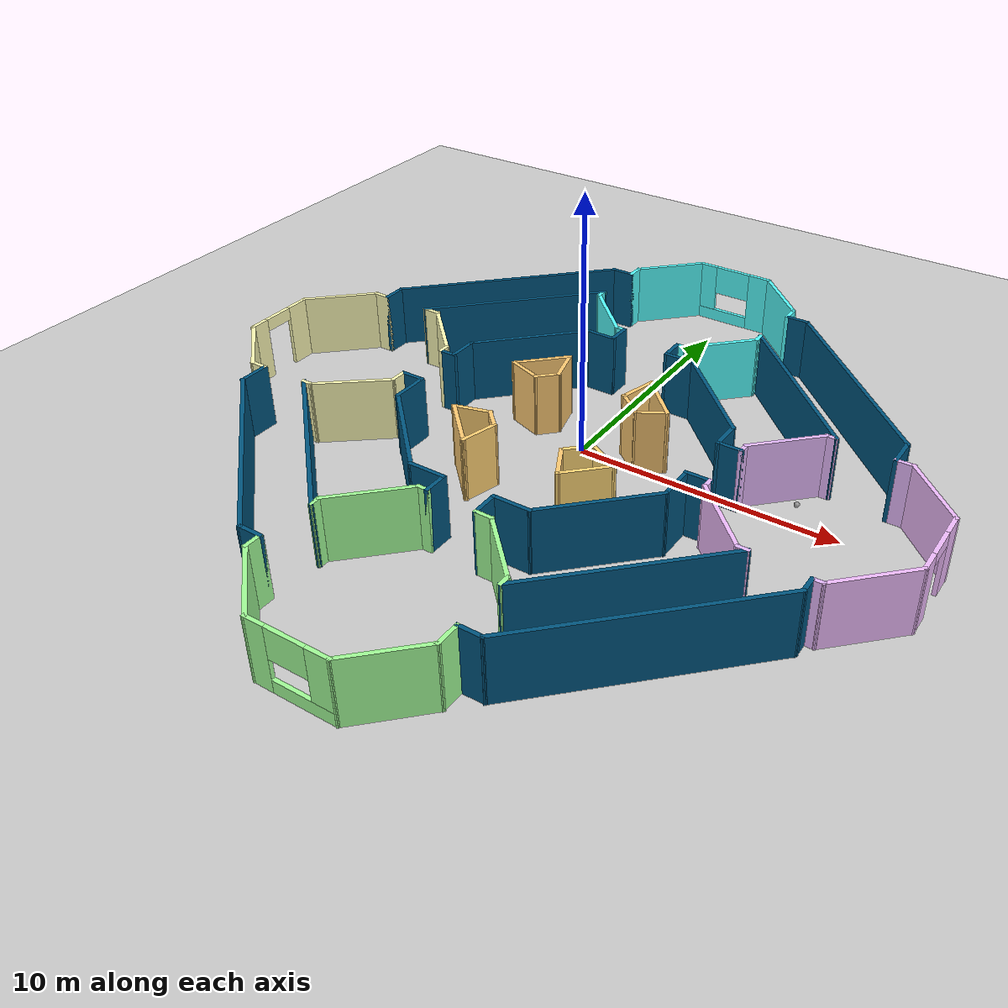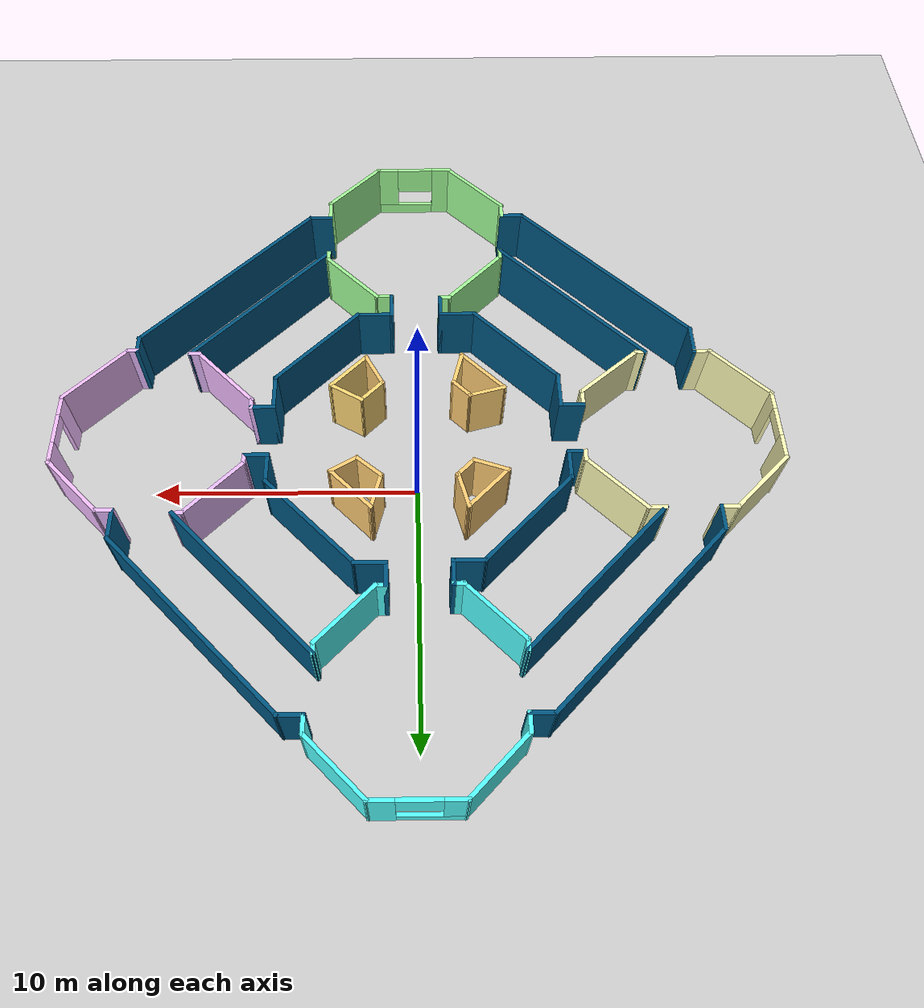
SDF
<sdf version="1.6">
 <world name="default">
  <light name="sun" type="directional">
   <pose>0 0 10 0 -0 0</pose>
   <diffuse>0.8 0.8 0.8 1</diffuse>
   <specular>0.2 0.2 0.2 1</specular>
   <attenuation>
    <range>1000</range>
    <constant>0.9</constant>
    <linear>0.01</linear>
    <quadratic>0.001</quadratic>
   </attenuation>
   <direction>-0.5 0.1 -0.9</direction>
  </light>
  <model name="ground_plane">
   <static>1</static>
   <link name="link">
    <collision name="collision">
     <geometry><plane><normal>0 0 1</normal><size>100 100</size></plane></geometry>
     <surface>
      <contact><collide_bitmask>65535</collide_bitmask></contact>
      <friction><ode><mu>100</mu><mu2>50</mu2></ode></friction>
     </surface>
    </collision>
    <visual name="visual">
     <cast_shadows>0</cast_shadows>
     <geometry><plane><normal>0 0 1</normal><size>100 100</size></plane></geometry>
     <material>
      <script><uri>file://media/materials/scripts/gazebo.material</uri><name>Gazebo/Grey</name></script>
     </material>
    </visual>
   </link>
  </model>
  <gravity>0 0 -9.8</gravity>
  <magnetic_field>6e-06 2.3e-05 -4.2e-05</magnetic_field>
  <atmosphere type="adiabatic"/>
  <physics name="default_physics" default="0" type="ode">
   <max_step_size>0.001</max_step_size>
   <real_time_factor>1</real_time_factor>
   <real_time_update_rate>1000</real_time_update_rate>
  </physics>
  <scene><ambient>0.4 0.4 0.4 1</ambient><background>0.7 0.7 0.7 1</background><shadows>1</shadows></scene>
  <spherical_coordinates>
   <surface_model>EARTH_WGS84</surface_model>
   <latitude_deg>0</latitude_deg>
   <longitude_deg>0</longitude_deg>
   <elevation>0</elevation>
   <heading_deg>0</heading_deg>
  </spherical_coordinates>
  <model name="building">
   <pose>-0.001846 -1.5065 0 0 -0 0</pose>
   <link name="Wall_0">
    <collision name="Wall_0_Collision">
     <geometry><box><size>2.25 0.15 2.5</size></box></geometry>
     <pose>0 0 1.25 0 -0 0</pose>
    </collision>
    <visual name="Wall_0_Visual">
     <pose>0 0 1.25 0 -0 0</pose>
     <geometry><box><size>2.25 0.15 2.5</size></box></geometry>
     <material>
      <script><uri>file://media/materials/scripts/gazebo.material</uri><name>Gazebo/Grey</name></script>
      <ambient>1 0.8 0.454902 1</ambient>
     </material>
     <meta><layer>0</layer></meta>
    </visual>
    <pose>-2.5367 2.70977 0 0 -0 0.785398</pose>
   </link>
   <link name="Wall_1">
    <collision name="Wall_1_Collision">
     <geometry><box><size>1.5 0.15 2.5</size></box></geometry>
     <pose>0 0 1.25 0 -0 0</pose>
    </collision>
    <visual name="Wall_1_Visual">
     <pose>0 0 1.25 0 -0 0</pose>
     <geometry><box><size>1.5 0.15 2.5</size></box></geometry>
     <material>
      <script><uri>file://media/materials/scripts/gazebo.material</uri><name>Gazebo/Grey</name></script>
      <ambient>1 0.8 0.454902 1</ambient>
     </material>
     <meta><layer>0</layer></meta>
    </visual>
    <pose>-1.61953 2.80023 0 0 0 -1.309</pose>
   </link>
   <link name="Wall_10">
    <collision name="Wall_10_Collision">
     <geometry><box><size>1.5 0.15 2.5</size></box></geometry>
     <pose>0 0 1.25 0 -0 0</pose>
    </collision>
    <visual name="Wall_10_Visual">
     <pose>0 0 1.25 0 -0 0</pose>
     <geometry><box><size>1.5 0.15 2.5</size></box></geometry>
     <material>
      <script><uri>file://media/materials/scripts/gazebo.material</uri><name>Gazebo/Grey</name></script>
      <ambient>1 0.819608 0.45098 1</ambient>
     </material>
     <meta><layer>0</layer></meta>
    </visual>
    <pose>-2.66214 -1.49592 0 0 -0 0.261799</pose>
   </link>
   <link name="Wall_100">
    <collision name="Wall_100_Collision">
     <geometry><box><size>0.75 0.15 2.5</size></box></geometry>
     <pose>0 0 1.25 0 -0 0</pose>
    </collision>
    <visual name="Wall_100_Visual">
     <pose>0 0 1.25 0 -0 0</pose>
     <geometry><box><size>0.75 0.15 2.5</size></box></geometry>
     <material>
      <script><uri>file://media/materials/scripts/gazebo.material</uri><name>Gazebo/Grey</name></script>
      <ambient>0.333333 1 1 1</ambient>
     </material>
     <meta><layer>0</layer></meta>
    </visual>
    <pose>3.70542 11.1499 0 0 -0 1.5708</pose>
   </link>
   <link name="Wall_101">
    <collision name="Wall_101_Collision">
     <geometry><box><size>3 0.15 2.5</size></box></geometry>
     <pose>0 0 1.25 0 -0 0</pose>
    </collision>
    <visual name="Wall_101_Visual">
     <pose>0 0 1.25 0 -0 0</pose>
     <geometry><box><size>3 0.15 2.5</size></box></geometry>
     <material>
      <script><uri>file://media/materials/scripts/gazebo.material</uri><name>Gazebo/Grey</name></script>
      <ambient>0.333333 1 1 1</ambient>
     </material>
     <meta><layer>0</layer></meta>
    </visual>
    <pose>2.69779 12.4576 0 0 -0 2.35619</pose>
   </link>
   <link name="Wall_102">
    <pose>0.140165 13.4652 0 0 -0 3.14159</pose>
    <visual name="Wall_102_Visual_0">
     <pose>-1.15171 0 1.25 0 -0 0</pose>
     <geometry><box><size>0.946574 0.15 2.5</size></box></geometry>
     <material>
      <script><uri>file://media/materials/scripts/gazebo.material</uri><name>Gazebo/Grey</name></script>
      <ambient>0.333333 1 1 1</ambient>
     </material>
     <meta><layer>0</layer></meta>
    </visual>
    <collision name="Wall_102_Collision_0">
     <geometry><box><size>0.946574 0.15 2.5</size></box></geometry>
     <pose>-1.15171 0 1.25 0 -0 0</pose>
    </collision>
    <visual name="Wall_102_Visual_1">
     <pose>0.473287 0 0.25 0 -0 0</pose>
     <geometry><box><size>2.30343 0.15 0.5</size></box></geometry>
     <material>
      <script><uri>file://media/materials/scripts/gazebo.material</uri><name>Gazebo/Grey</name></script>
      <ambient>0.333333 1 1 1</ambient>
     </material>
     <meta><layer>0</layer></meta>
    </visual>
    <collision name="Wall_102_Collision_1">
     <geometry><box><size>2.30343 0.15 0.5</size></box></geometry>
     <pose>0.473287 0 0.25 0 -0 0</pose>
    </collision>
    <visual name="Wall_102_Visual_2">
     <pose>1.22329 0 1.5 0 -0 0</pose>
     <geometry><box><size>0.803426 0.15 2</size></box></geometry>
     <material>
      <script><uri>file://media/materials/scripts/gazebo.material</uri><name>Gazebo/Grey</name></script>
      <ambient>0.333333 1 1 1</ambient>
     </material>
     <meta><layer>0</layer></meta>
    </visual>
    <collision name="Wall_102_Collision_2">
     <geometry><box><size>0.803426 0.15 2</size></box></geometry>
     <pose>1.22329 0 1.5 0 -0 0</pose>
    </collision>
    <visual name="Wall_102_Visual_3">
     <pose>0.071574 0 1.9 0 -0 0</pose>
     <geometry><box><size>1.5 0.15 1.2</size></box></geometry>
     <material>
      <script><uri>file://media/materials/scripts/gazebo.material</uri><name>Gazebo/Grey</name></script>
      <ambient>0.333333 1 1 1</ambient>
     </material>
     <meta><layer>0</layer></meta>
    </visual>
    <collision name="Wall_102_Collision_3">
     <geometry><box><size>1.5 0.15 1.2</size></box></geometry>
     <pose>0.071574 0 1.9 0 -0 0</pose>
    </collision>
   </link>
   <link name="Wall_103">
    <collision name="Wall_103_Collision">
     <geometry><box><size>3 0.15 2.5</size></box></geometry>
     <pose>0 0 1.25 0 -0 0</pose>
    </collision>
    <visual name="Wall_103_Visual">
     <pose>0 0 1.25 0 -0 0</pose>
     <geometry><box><size>3 0.15 2.5</size></box></geometry>
     <material>
      <script><uri>file://media/materials/scripts/gazebo.material</uri><name>Gazebo/Grey</name></script>
      <ambient>0.333333 1 1 1</ambient>
     </material>
     <meta><layer>0</layer></meta>
    </visual>
    <pose>-2.41746 12.4576 0 0 0 -2.35619</pose>
   </link>
   <link name="Wall_104">
    <collision name="Wall_104_Collision">
     <geometry><box><size>0.75 0.15 2.5</size></box></geometry>
     <pose>0 0 1.25 0 -0 0</pose>
    </collision>
    <visual name="Wall_104_Visual">
     <pose>0 0 1.25 0 -0 0</pose>
     <geometry><box><size>0.75 0.15 2.5</size></box></geometry>
     <material>
      <script><uri>file://media/materials/scripts/gazebo.material</uri><name>Gazebo/Grey</name></script>
      <ambient>0.333333 1 1 1</ambient>
     </material>
     <meta><layer>0</layer></meta>
    </visual>
    <pose>-3.42509 11.1499 0 0 0 -1.5708</pose>
   </link>
   <link name="Wall_105">
    <collision name="Wall_105_Collision">
     <geometry><box><size>1 0.15 2.5</size></box></geometry>
     <pose>0 0 1.25 0 -0 0</pose>
    </collision>
    <visual name="Wall_105_Visual">
     <pose>0 0 1.25 0 -0 0</pose>
     <geometry><box><size>1 0.15 2.5</size></box></geometry>
     <material>
      <script><uri>file://media/materials/scripts/gazebo.material</uri><name>Gazebo/Grey</name></script>
      <ambient>0 0.333333 0.498039 1</ambient>
     </material>
     <meta><layer>0</layer></meta>
    </visual>
    <pose>-3.85009 10.8499 0 0 -0 3.14159</pose>
   </link>
   <link name="Wall_106">
    <collision name="Wall_106_Collision">
     <geometry><box><size>9.25 0.15 2.5</size></box></geometry>
     <pose>0 0 1.25 0 -0 0</pose>
    </collision>
    <visual name="Wall_106_Visual">
     <pose>0 0 1.25 0 -0 0</pose>
     <geometry><box><size>9.25 0.15 2.5</size></box></geometry>
     <material>
      <script><uri>file://media/materials/scripts/gazebo.material</uri><name>Gazebo/Grey</name></script>
      <ambient>0 0.333333 0.498039 1</ambient>
     </material>
     <meta><layer>0</layer></meta>
    </visual>
    <pose>-7.49242 7.63259 0 0 0 -2.35619</pose>
   </link>
   <link name="Wall_107">
    <collision name="Wall_107_Collision">
     <geometry><box><size>1 0.15 2.5</size></box></geometry>
     <pose>0 0 1.25 0 -0 0</pose>
    </collision>
    <visual name="Wall_107_Visual">
     <pose>0 0 1.25 0 -0 0</pose>
     <geometry><box><size>1 0.15 2.5</size></box></geometry>
     <material>
      <script><uri>file://media/materials/scripts/gazebo.material</uri><name>Gazebo/Grey</name></script>
      <ambient>0 0.333333 0.498039 1</ambient>
     </material>
     <meta><layer>0</layer></meta>
    </visual>
    <pose>-10.7098 3.99025 0 0 0 -1.5708</pose>
   </link>
   <link name="Wall_108">
    <collision name="Wall_108_Collision">
     <geometry><box><size>0.75 0.15 2.5</size></box></geometry>
     <pose>0 0 1.25 0 -0 0</pose>
    </collision>
    <visual name="Wall_108_Visual">
     <pose>0 0 1.25 0 -0 0</pose>
     <geometry><box><size>0.75 0.15 2.5</size></box></geometry>
     <material>
      <script><uri>file://media/materials/scripts/gazebo.material</uri><name>Gazebo/Grey</name></script>
      <ambient>1 0.992157 0.717647 1</ambient>
     </material>
     <meta><layer>0</layer></meta>
    </visual>
    <pose>-11.0098 3.56525 0 0 -0 3.14159</pose>
   </link>
   <link name="Wall_109">
    <collision name="Wall_109_Collision">
     <geometry><box><size>3.07414 0.15 2.5</size></box></geometry>
     <pose>0 0 1.25 0 -0 0</pose>
    </collision>
    <visual name="Wall_109_Visual">
     <pose>0 0 1.25 0 -0 0</pose>
     <geometry><box><size>3.07414 0.15 2.5</size></box></geometry>
     <material>
      <script><uri>file://media/materials/scripts/gazebo.material</uri><name>Gazebo/Grey</name></script>
      <ambient>1 0.992157 0.717647 1</ambient>
     </material>
     <meta><layer>0</layer></meta>
    </visual>
    <pose>-12.3692 2.55763 0 0 0 -2.38124</pose>
   </link>
   <link name="Wall_11">
    <collision name="Wall_11_Collision">
     <geometry><box><size>1 0.15 2.5</size></box></geometry>
     <pose>0 0 1.25 0 -0 0</pose>
    </collision>
    <visual name="Wall_11_Visual">
     <pose>0 0 1.25 0 -0 0</pose>
     <geometry><box><size>1 0.15 2.5</size></box></geometry>
     <material>
      <script><uri>file://media/materials/scripts/gazebo.material</uri><name>Gazebo/Grey</name></script>
      <ambient>1 0.8 0.454902 1</ambient>
     </material>
     <meta><layer>0</layer></meta>
    </visual>
    <pose>-1.70962 -1.62174 0 0 0 -0.785398</pose>
   </link>
   <link name="Wall_12">
    <collision name="Wall_12_Collision">
     <geometry><box><size>1.5 0.15 2.5</size></box></geometry>
     <pose>0 0 1.25 0 -0 0</pose>
    </collision>
    <visual name="Wall_12_Visual">
     <pose>0 0 1.25 0 -0 0</pose>
     <geometry><box><size>1.5 0.15 2.5</size></box></geometry>
     <material>
      <script><uri>file://media/materials/scripts/gazebo.material</uri><name>Gazebo/Grey</name></script>
      <ambient>1 0.819608 0.45098 1</ambient>
     </material>
     <meta><layer>0</layer></meta>
    </visual>
    <pose>-1.5838 -2.57426 0 0 0 -1.8326</pose>
   </link>
   <link name="Wall_13">
    <collision name="Wall_13_Collision">
     <geometry><box><size>2.35 0.15 2.5</size></box></geometry>
     <pose>0 0 1.25 0 -0 0</pose>
    </collision>
    <visual name="Wall_13_Visual">
     <pose>0 0 1.25 0 -0 0</pose>
     <geometry><box><size>2.35 0.15 2.5</size></box></geometry>
     <material>
      <script><uri>file://media/materials/scripts/gazebo.material</uri><name>Gazebo/Grey</name></script>
      <ambient>1 0.8 0.454902 1</ambient>
     </material>
     <meta><layer>0</layer></meta>
    </visual>
    <pose>-2.53633 -2.44844 0 0 -0 2.35619</pose>
   </link>
   <link name="Wall_15">
    <collision name="Wall_15_Collision">
     <geometry><box><size>1.25 0.15 2.5</size></box></geometry>
     <pose>0 0 1.25 0 -0 0</pose>
    </collision>
    <visual name="Wall_15_Visual">
     <pose>0 0 1.25 0 -0 0</pose>
     <geometry><box><size>1.25 0.15 2.5</size></box></geometry>
     <material>
      <script><uri>file://media/materials/scripts/gazebo.material</uri><name>Gazebo/Grey</name></script>
      <ambient>1 0.847059 0.458824 1</ambient>
     </material>
     <meta><layer>0</layer></meta>
    </visual>
    <pose>1.70963 -1.54407 0 0 -0 0.785398</pose>
   </link>
   <link name="Wall_16">
    <collision name="Wall_16_Collision">
     <geometry><box><size>1.5 0.15 2.5</size></box></geometry>
     <pose>0 0 1.25 0 -0 0</pose>
    </collision>
    <visual name="Wall_16_Visual">
     <pose>0 0 1.25 0 -0 0</pose>
     <geometry><box><size>1.5 0.15 2.5</size></box></geometry>
     <material>
      <script><uri>file://media/materials/scripts/gazebo.material</uri><name>Gazebo/Grey</name></script>
      <ambient>1 0.847059 0.458824 1</ambient>
     </material>
     <meta><layer>0</layer></meta>
    </visual>
    <pose>2.68311 -1.49266 0 0 0 -0.523599</pose>
   </link>
   <link name="Wall_17">
    <collision name="Wall_17_Collision">
     <geometry><box><size>2 0.15 2.5</size></box></geometry>
     <pose>0 0 1.25 0 -0 0</pose>
    </collision>
    <visual name="Wall_17_Visual">
     <pose>0 0 1.25 0 -0 0</pose>
     <geometry><box><size>2 0.15 2.5</size></box></geometry>
     <material>
      <script><uri>file://media/materials/scripts/gazebo.material</uri><name>Gazebo/Grey</name></script>
      <ambient>1 0.847059 0.458824 1</ambient>
     </material>
     <meta><layer>0</layer></meta>
    </visual>
    <pose>2.6136 -2.48423 0 0 0 -2.35619</pose>
   </link>
   <link name="Wall_18">
    <collision name="Wall_18_Collision">
     <geometry><box><size>1.51415 0.15 2.5</size></box></geometry>
     <pose>0 0 1.25 0 -0 0</pose>
    </collision>
    <visual name="Wall_18_Visual">
     <pose>0 0 1.25 0 -0 0</pose>
     <geometry><box><size>1.51415 0.15 2.5</size></box></geometry>
     <material>
      <script><uri>file://media/materials/scripts/gazebo.material</uri><name>Gazebo/Grey</name></script>
      <ambient>1 0.8 0.454902 1</ambient>
     </material>
     <meta><layer>0</layer></meta>
    </visual>
    <pose>1.64013 -2.53564 0 0 -0 2.05814</pose>
   </link>
   <link name="Wall_2">
    <collision name="Wall_2_Collision">
     <geometry><box><size>1 0.15 2.5</size></box></geometry>
     <pose>0 0 1.25 0 -0 0</pose>
    </collision>
    <visual name="Wall_2_Visual">
     <pose>0 0 1.25 0 -0 0</pose>
     <geometry><box><size>1 0.15 2.5</size></box></geometry>
     <material>
      <script><uri>file://media/materials/scripts/gazebo.material</uri><name>Gazebo/Grey</name></script>
      <ambient>1 0.8 0.454902 1</ambient>
     </material>
     <meta><layer>0</layer></meta>
    </visual>
    <pose>-1.74535 1.84771 0 0 0 -2.35619</pose>
   </link>
   <link name="Wall_20">
    <collision name="Wall_20_Collision">
     <geometry><box><size>1.5 0.15 2.5</size></box></geometry>
     <pose>0 0 1.25 0 -0 0</pose>
    </collision>
    <visual name="Wall_20_Visual">
     <pose>0 0 1.25 0 -0 0</pose>
     <geometry><box><size>1.5 0.15 2.5</size></box></geometry>
     <material>
      <script><uri>file://media/materials/scripts/gazebo.material</uri><name>Gazebo/Grey</name></script>
      <ambient>0 0.333333 0.498039 1</ambient>
     </material>
     <meta><layer>0</layer></meta>
    </visual>
    <pose>-5.40602 -1.52769 0 0 0 -1.5708</pose>
   </link>
   <link name="Wall_21">
    <collision name="Wall_21_Collision">
     <geometry><box><size>4.5 0.15 2.5</size></box></geometry>
     <pose>0 0 1.25 0 -0 0</pose>
    </collision>
    <visual name="Wall_21_Visual">
     <pose>0 0 1.25 0 -0 0</pose>
     <geometry><box><size>4.5 0.15 2.5</size></box></geometry>
     <material>
      <script><uri>file://media/materials/scripts/gazebo.material</uri><name>Gazebo/Grey</name></script>
      <ambient>0 0.333333 0.498039 1</ambient>
     </material>
     <meta><layer>0</layer></meta>
    </visual>
    <pose>-3.86807 -3.74065 0 0 0 -0.785398</pose>
   </link>
   <link name="Wall_22">
    <collision name="Wall_22_Collision">
     <geometry><box><size>1.5 0.15 2.5</size></box></geometry>
     <pose>0 0 1.25 0 -0 0</pose>
    </collision>
    <visual name="Wall_22_Visual">
     <pose>0 0 1.25 0 -0 0</pose>
     <geometry><box><size>1.5 0.15 2.5</size></box></geometry>
     <material>
      <script><uri>file://media/materials/scripts/gazebo.material</uri><name>Gazebo/Grey</name></script>
      <ambient>0 0.333333 0.498039 1</ambient>
     </material>
     <meta><layer>0</layer></meta>
    </visual>
    <pose>-1.65511 -5.2786 0 0 -0 0</pose>
   </link>
   <link name="Wall_23">
    <collision name="Wall_23_Collision">
     <geometry><box><size>1 0.15 2.5</size></box></geometry>
     <pose>0 0 1.25 0 -0 0</pose>
    </collision>
    <visual name="Wall_23_Visual">
     <pose>0 0 1.25 0 -0 0</pose>
     <geometry><box><size>1 0.15 2.5</size></box></geometry>
     <material>
      <script><uri>file://media/materials/scripts/gazebo.material</uri><name>Gazebo/Grey</name></script>
      <ambient>0 0.333333 0.498039 1</ambient>
     </material>
     <meta><layer>0</layer></meta>
    </visual>
    <pose>-0.980109 -5.7036 0 0 0 -1.5708</pose>
   </link>
   <link name="Wall_24">
    <collision name="Wall_24_Collision">
     <geometry><box><size>0.5 0.15 2.5</size></box></geometry>
     <pose>0 0 1.25 0 -0 0</pose>
    </collision>
    <visual name="Wall_24_Visual">
     <pose>0 0 1.25 0 -0 0</pose>
     <geometry><box><size>0.5 0.15 2.5</size></box></geometry>
     <material>
      <script><uri>file://media/materials/scripts/gazebo.material</uri><name>Gazebo/Grey</name></script>
      <ambient>0.639216 1 0.6 1</ambient>
     </material>
     <meta><layer>0</layer></meta>
    </visual>
    <pose>-1.15511 -6.1286 0 0 -0 3.14159</pose>
   </link>
   <link name="Wall_26">
    <collision name="Wall_26_Collision">
     <geometry><box><size>1 0.15 2.5</size></box></geometry>
     <pose>0 0 1.25 0 -0 0</pose>
    </collision>
    <visual name="Wall_26_Visual">
     <pose>0 0 1.25 0 -0 0</pose>
     <geometry><box><size>1 0.15 2.5</size></box></geometry>
     <material>
      <script><uri>file://media/materials/scripts/gazebo.material</uri><name>Gazebo/Grey</name></script>
      <ambient>0 0.333333 0.498039 1</ambient>
     </material>
     <meta><layer>0</layer></meta>
    </visual>
    <pose>-5.83102 -0.852688 0 0 -0 3.14159</pose>
   </link>
   <link name="Wall_27">
    <collision name="Wall_27_Collision">
     <geometry><box><size>0.75 0.15 2.5</size></box></geometry>
     <pose>0 0 1.25 0 -0 0</pose>
    </collision>
    <visual name="Wall_27_Visual">
     <pose>0 0 1.25 0 -0 0</pose>
     <geometry><box><size>0.75 0.15 2.5</size></box></geometry>
     <material>
      <script><uri>file://media/materials/scripts/gazebo.material</uri><name>Gazebo/Grey</name></script>
      <ambient>1 0.992157 0.717647 1</ambient>
     </material>
     <meta><layer>0</layer></meta>
    </visual>
    <pose>-6.25602 -1.15269 0 0 0 -1.5708</pose>
   </link>
   <link name="Wall_29">
    <collision name="Wall_29_Collision">
     <geometry><box><size>1.5 0.15 2.5</size></box></geometry>
     <pose>0 0 1.25 0 -0 0</pose>
    </collision>
    <visual name="Wall_29_Visual">
     <pose>0 0 1.25 0 -0 0</pose>
     <geometry><box><size>1.5 0.15 2.5</size></box></geometry>
     <material>
      <script><uri>file://media/materials/scripts/gazebo.material</uri><name>Gazebo/Grey</name></script>
      <ambient>0 0.333333 0.498039 1</ambient>
     </material>
     <meta><layer>0</layer></meta>
    </visual>
    <pose>1.65302 -5.27063 0 0 -0 0</pose>
   </link>
   <link name="Wall_3">
    <collision name="Wall_3_Collision">
     <geometry><box><size>1.45288 0.15 2.5</size></box></geometry>
     <pose>0 0 1.25 0 -0 0</pose>
    </collision>
    <visual name="Wall_3_Visual">
     <pose>0 0 1.25 0 -0 0</pose>
     <geometry><box><size>1.45288 0.15 2.5</size></box></geometry>
     <material>
      <script><uri>file://media/materials/scripts/gazebo.material</uri><name>Gazebo/Grey</name></script>
      <ambient>1 0.8 0.454902 1</ambient>
     </material>
     <meta><layer>0</layer></meta>
    </visual>
    <pose>-2.66252 1.75725 0 0 -0 2.81327</pose>
   </link>
   <link name="Wall_30">
    <collision name="Wall_30_Collision">
     <geometry><box><size>4.5 0.15 2.5</size></box></geometry>
     <pose>0 0 1.25 0 -0 0</pose>
    </collision>
    <visual name="Wall_30_Visual">
     <pose>0 0 1.25 0 -0 0</pose>
     <geometry><box><size>4.5 0.15 2.5</size></box></geometry>
     <material>
      <script><uri>file://media/materials/scripts/gazebo.material</uri><name>Gazebo/Grey</name></script>
      <ambient>0 0.333333 0.498039 1</ambient>
     </material>
     <meta><layer>0</layer></meta>
    </visual>
    <pose>3.86598 -3.73268 0 0 -0 0.785398</pose>
   </link>
   <link name="Wall_31">
    <collision name="Wall_31_Collision">
     <geometry><box><size>1.5 0.15 2.5</size></box></geometry>
     <pose>0 0 1.25 0 -0 0</pose>
    </collision>
    <visual name="Wall_31_Visual">
     <pose>0 0 1.25 0 -0 0</pose>
     <geometry><box><size>1.5 0.15 2.5</size></box></geometry>
     <material>
      <script><uri>file://media/materials/scripts/gazebo.material</uri><name>Gazebo/Grey</name></script>
      <ambient>0 0.333333 0.498039 1</ambient>
     </material>
     <meta><layer>0</layer></meta>
    </visual>
    <pose>5.40394 -1.51972 0 0 -0 1.5708</pose>
   </link>
   <link name="Wall_32">
    <collision name="Wall_32_Collision">
     <geometry><box><size>1 0.15 2.5</size></box></geometry>
     <pose>0 0 1.25 0 -0 0</pose>
    </collision>
    <visual name="Wall_32_Visual">
     <pose>0 0 1.25 0 -0 0</pose>
     <geometry><box><size>1 0.15 2.5</size></box></geometry>
     <material>
      <script><uri>file://media/materials/scripts/gazebo.material</uri><name>Gazebo/Grey</name></script>
      <ambient>0 0.333333 0.498039 1</ambient>
     </material>
     <meta><layer>0</layer></meta>
    </visual>
    <pose>5.82894 -0.84472 0 0 -0 0</pose>
   </link>
   <link name="Wall_33">
    <collision name="Wall_33_Collision">
     <geometry><box><size>0.5 0.15 2.5</size></box></geometry>
     <pose>0 0 1.25 0 -0 0</pose>
    </collision>
    <visual name="Wall_33_Visual">
     <pose>0 0 1.25 0 -0 0</pose>
     <geometry><box><size>0.5 0.15 2.5</size></box></geometry>
     <material>
      <script><uri>file://media/materials/scripts/gazebo.material</uri><name>Gazebo/Grey</name></script>
      <ambient>0.913725 0.737255 1 1</ambient>
     </material>
     <meta><layer>0</layer></meta>
    </visual>
    <pose>6.25394 -1.01972 0 0 0 -1.5708</pose>
   </link>
   <link name="Wall_35">
    <collision name="Wall_35_Collision">
     <geometry><box><size>0.5 0.15 2.5</size></box></geometry>
     <pose>0 0 1.25 0 -0 0</pose>
    </collision>
    <visual name="Wall_35_Visual">
     <pose>0 0 1.25 0 -0 0</pose>
     <geometry><box><size>0.5 0.15 2.5</size></box></geometry>
     <material>
      <script><uri>file://media/materials/scripts/gazebo.material</uri><name>Gazebo/Grey</name></script>
      <ambient>0.333333 1 1 1</ambient>
     </material>
     <meta><layer>0</layer></meta>
    </visual>
    <pose>1.3119 6.45658 0 0 -0 3.14159</pose>
   </link>
   <link name="Wall_36">
    <collision name="Wall_36_Collision">
     <geometry><box><size>1 0.15 2.5</size></box></geometry>
     <pose>0 0 1.25 0 -0 0</pose>
    </collision>
    <visual name="Wall_36_Visual">
     <pose>0 0 1.25 0 -0 0</pose>
     <geometry><box><size>1 0.15 2.5</size></box></geometry>
     <material>
      <script><uri>file://media/materials/scripts/gazebo.material</uri><name>Gazebo/Grey</name></script>
      <ambient>0 0.333333 0.498039 1</ambient>
     </material>
     <meta><layer>0</layer></meta>
    </visual>
    <pose>1.1369 6.03158 0 0 0 -1.5708</pose>
   </link>
   <link name="Wall_37">
    <collision name="Wall_37_Collision">
     <geometry><box><size>1.25 0.15 2.5</size></box></geometry>
     <pose>0 0 1.25 0 -0 0</pose>
    </collision>
    <visual name="Wall_37_Visual">
     <pose>0 0 1.25 0 -0 0</pose>
     <geometry><box><size>1.25 0.15 2.5</size></box></geometry>
     <material>
      <script><uri>file://media/materials/scripts/gazebo.material</uri><name>Gazebo/Grey</name></script>
      <ambient>0 0.333333 0.498039 1</ambient>
     </material>
     <meta><layer>0</layer></meta>
    </visual>
    <pose>1.6869 5.60658 0 0 -0 0</pose>
   </link>
   <link name="Wall_38">
    <collision name="Wall_38_Collision">
     <geometry><box><size>4.75 0.15 2.5</size></box></geometry>
     <pose>0 0 1.25 0 -0 0</pose>
    </collision>
    <visual name="Wall_38_Visual">
     <pose>0 0 1.25 0 -0 0</pose>
     <geometry><box><size>4.75 0.15 2.5</size></box></geometry>
     <material>
      <script><uri>file://media/materials/scripts/gazebo.material</uri><name>Gazebo/Grey</name></script>
      <ambient>0 0.333333 0.498039 1</ambient>
     </material>
     <meta><layer>0</layer></meta>
    </visual>
    <pose>3.86324 3.98024 0 0 0 -0.785398</pose>
   </link>
   <link name="Wall_39">
    <collision name="Wall_39_Collision">
     <geometry><box><size>1.25 0.15 2.5</size></box></geometry>
     <pose>0 0 1.25 0 -0 0</pose>
    </collision>
    <visual name="Wall_39_Visual">
     <pose>0 0 1.25 0 -0 0</pose>
     <geometry><box><size>1.25 0.15 2.5</size></box></geometry>
     <material>
      <script><uri>file://media/materials/scripts/gazebo.material</uri><name>Gazebo/Grey</name></script>
      <ambient>0 0.333333 0.498039 1</ambient>
     </material>
     <meta><layer>0</layer></meta>
    </visual>
    <pose>5.48959 1.80389 0 0 0 -1.5708</pose>
   </link>
   <link name="Wall_42">
    <collision name="Wall_42_Collision">
     <geometry><box><size>1 0.15 2.5</size></box></geometry>
     <pose>0 0 1.25 0 -0 0</pose>
    </collision>
    <visual name="Wall_42_Visual">
     <pose>0 0 1.25 0 -0 0</pose>
     <geometry><box><size>1 0.15 2.5</size></box></geometry>
     <material>
      <script><uri>file://media/materials/scripts/gazebo.material</uri><name>Gazebo/Grey</name></script>
      <ambient>0 0.333333 0.498039 1</ambient>
     </material>
     <meta><layer>0</layer></meta>
    </visual>
    <pose>5.91459 1.25389 0 0 -0 0</pose>
   </link>
   <link name="Wall_43">
    <collision name="Wall_43_Collision">
     <geometry><box><size>0.5 0.15 2.5</size></box></geometry>
     <pose>0 0 1.25 0 -0 0</pose>
    </collision>
    <visual name="Wall_43_Visual">
     <pose>0 0 1.25 0 -0 0</pose>
     <geometry><box><size>0.5 0.15 2.5</size></box></geometry>
     <material>
      <script><uri>file://media/materials/scripts/gazebo.material</uri><name>Gazebo/Grey</name></script>
      <ambient>0.913725 0.737255 1 1</ambient>
     </material>
     <meta><layer>0</layer></meta>
    </visual>
    <pose>6.33959 1.42889 0 0 -0 1.5708</pose>
   </link>
   <link name="Wall_45">
    <collision name="Wall_45_Collision">
     <geometry><box><size>0.5 0.15 2.5</size></box></geometry>
     <pose>0 0 1.25 0 -0 0</pose>
    </collision>
    <visual name="Wall_45_Visual">
     <pose>0 0 1.25 0 -0 0</pose>
     <geometry><box><size>0.5 0.15 2.5</size></box></geometry>
     <material>
      <script><uri>file://media/materials/scripts/gazebo.material</uri><name>Gazebo/Grey</name></script>
      <ambient>0.333333 1 1 1</ambient>
     </material>
     <meta><layer>0</layer></meta>
    </visual>
    <pose>-1.34508 6.41032 0 0 -0 0</pose>
   </link>
   <link name="Wall_46">
    <collision name="Wall_46_Collision">
     <geometry><box><size>1 0.15 2.5</size></box></geometry>
     <pose>0 0 1.25 0 -0 0</pose>
    </collision>
    <visual name="Wall_46_Visual">
     <pose>0 0 1.25 0 -0 0</pose>
     <geometry><box><size>1 0.15 2.5</size></box></geometry>
     <material>
      <script><uri>file://media/materials/scripts/gazebo.material</uri><name>Gazebo/Grey</name></script>
      <ambient>0 0.333333 0.498039 1</ambient>
     </material>
     <meta><layer>0</layer></meta>
    </visual>
    <pose>-1.17008 5.98532 0 0 0 -1.5708</pose>
   </link>
   <link name="Wall_47">
    <collision name="Wall_47_Collision">
     <geometry><box><size>1.25 0.15 2.5</size></box></geometry>
     <pose>0 0 1.25 0 -0 0</pose>
    </collision>
    <visual name="Wall_47_Visual">
     <pose>0 0 1.25 0 -0 0</pose>
     <geometry><box><size>1.25 0.15 2.5</size></box></geometry>
     <material>
      <script><uri>file://media/materials/scripts/gazebo.material</uri><name>Gazebo/Grey</name></script>
      <ambient>0 0.333333 0.498039 1</ambient>
     </material>
     <meta><layer>0</layer></meta>
    </visual>
    <pose>-1.72008 5.56032 0 0 -0 3.14159</pose>
   </link>
   <link name="Wall_48">
    <collision name="Wall_48_Collision">
     <geometry><box><size>4.75 0.15 2.5</size></box></geometry>
     <pose>0 0 1.25 0 -0 0</pose>
    </collision>
    <visual name="Wall_48_Visual">
     <pose>0 0 1.25 0 -0 0</pose>
     <geometry><box><size>4.75 0.15 2.5</size></box></geometry>
     <material>
      <script><uri>file://media/materials/scripts/gazebo.material</uri><name>Gazebo/Grey</name></script>
      <ambient>0 0.333333 0.498039 1</ambient>
     </material>
     <meta><layer>0</layer></meta>
    </visual>
    <pose>-3.89643 3.93398 0 0 0 -2.35619</pose>
   </link>
   <link name="Wall_49">
    <collision name="Wall_49_Collision">
     <geometry><box><size>1.25 0.15 2.5</size></box></geometry>
     <pose>0 0 1.25 0 -0 0</pose>
    </collision>
    <visual name="Wall_49_Visual">
     <pose>0 0 1.25 0 -0 0</pose>
     <geometry><box><size>1.25 0.15 2.5</size></box></geometry>
     <material>
      <script><uri>file://media/materials/scripts/gazebo.material</uri><name>Gazebo/Grey</name></script>
      <ambient>0 0.333333 0.498039 1</ambient>
     </material>
     <meta><layer>0</layer></meta>
    </visual>
    <pose>-5.52277 1.75763 0 0 0 -1.5708</pose>
   </link>
   <link name="Wall_5">
    <collision name="Wall_5_Collision">
     <geometry><box><size>1.5 0.15 2.5</size></box></geometry>
     <pose>0 0 1.25 0 -0 0</pose>
    </collision>
    <visual name="Wall_5_Visual">
     <pose>0 0 1.25 0 -0 0</pose>
     <geometry><box><size>1.5 0.15 2.5</size></box></geometry>
     <material>
      <script><uri>file://media/materials/scripts/gazebo.material</uri><name>Gazebo/Grey</name></script>
      <ambient>1 0.8 0.454902 1</ambient>
     </material>
     <meta><layer>0</layer></meta>
    </visual>
    <pose>1.51292 2.79421 0 0 -0 1.309</pose>
   </link>
   <link name="Wall_50">
    <collision name="Wall_50_Collision">
     <geometry><box><size>0.75 0.15 2.5</size></box></geometry>
     <pose>0 0 1.25 0 -0 0</pose>
    </collision>
    <visual name="Wall_50_Visual">
     <pose>0 0 1.25 0 -0 0</pose>
     <geometry><box><size>0.75 0.15 2.5</size></box></geometry>
     <material>
      <script><uri>file://media/materials/scripts/gazebo.material</uri><name>Gazebo/Grey</name></script>
      <ambient>0 0.333333 0.498039 1</ambient>
     </material>
     <meta><layer>0</layer></meta>
    </visual>
    <pose>-5.82277 1.20763 0 0 -0 3.14159</pose>
   </link>
   <link name="Wall_51">
    <collision name="Wall_51_Collision">
     <geometry><box><size>0.5 0.15 2.5</size></box></geometry>
     <pose>0 0 1.25 0 -0 0</pose>
    </collision>
    <visual name="Wall_51_Visual">
     <pose>0 0 1.25 0 -0 0</pose>
     <geometry><box><size>0.5 0.15 2.5</size></box></geometry>
     <material>
      <script><uri>file://media/materials/scripts/gazebo.material</uri><name>Gazebo/Grey</name></script>
      <ambient>1 0.992157 0.717647 1</ambient>
     </material>
     <meta><layer>0</layer></meta>
    </visual>
    <pose>-6.12277 1.38263 0 0 -0 1.5708</pose>
   </link>
   <link name="Wall_52">
    <collision name="Wall_52_Collision">
     <geometry><box><size>3 0.15 2.5</size></box></geometry>
     <pose>0 0 1.25 0 -0 0</pose>
    </collision>
    <visual name="Wall_52_Visual">
     <pose>0 0 1.25 0 -0 0</pose>
     <geometry><box><size>3 0.15 2.5</size></box></geometry>
     <material>
      <script><uri>file://media/materials/scripts/gazebo.material</uri><name>Gazebo/Grey</name></script>
      <ambient>1 0.992157 0.717647 1</ambient>
     </material>
     <meta><layer>0</layer></meta>
    </visual>
    <pose>-7.1304 2.56526 0 0 -0 2.35619</pose>
   </link>
   <link name="Wall_53">
    <collision name="Wall_53_Collision">
     <geometry><box><size>0.75 0.15 2.5</size></box></geometry>
     <pose>0 0 1.25 0 -0 0</pose>
    </collision>
    <visual name="Wall_53_Visual">
     <pose>0 0 1.25 0 -0 0</pose>
     <geometry><box><size>0.75 0.15 2.5</size></box></geometry>
     <material>
      <script><uri>file://media/materials/scripts/gazebo.material</uri><name>Gazebo/Grey</name></script>
      <ambient>1 0.992157 0.717647 1</ambient>
     </material>
     <meta><layer>0</layer></meta>
    </visual>
    <pose>-8.43803 3.57289 0 0 -0 3.14159</pose>
   </link>
   <link name="Wall_54">
    <collision name="Wall_54_Collision">
     <geometry><box><size>7.5 0.15 2.5</size></box></geometry>
     <pose>0 0 1.25 0 -0 0</pose>
    </collision>
    <visual name="Wall_54_Visual">
     <pose>0 0 1.25 0 -0 0</pose>
     <geometry><box><size>7.5 0.15 2.5</size></box></geometry>
     <material>
      <script><uri>file://media/materials/scripts/gazebo.material</uri><name>Gazebo/Grey</name></script>
      <ambient>0 0.333333 0.498039 1</ambient>
     </material>
     <meta><layer>0</layer></meta>
    </visual>
    <pose>-6.13941 6.1715 0 0 -0 0.785398</pose>
   </link>
   <link name="Wall_55">
    <collision name="Wall_55_Collision">
     <geometry><box><size>0.5 0.15 2.5</size></box></geometry>
     <pose>0 0 1.25 0 -0 0</pose>
    </collision>
    <visual name="Wall_55_Visual">
     <pose>0 0 1.25 0 -0 0</pose>
     <geometry><box><size>0.5 0.15 2.5</size></box></geometry>
     <material>
      <script><uri>file://media/materials/scripts/gazebo.material</uri><name>Gazebo/Grey</name></script>
      <ambient>0.333333 1 1 1</ambient>
     </material>
     <meta><layer>0</layer></meta>
    </visual>
    <pose>-3.54079 8.59512 0 0 0 -1.5708</pose>
   </link>
   <link name="Wall_56">
    <collision name="Wall_56_Collision">
     <geometry><box><size>3.00001 0.15 2.5</size></box></geometry>
     <pose>0 0 1.25 0 -0 0</pose>
    </collision>
    <visual name="Wall_56_Visual">
     <pose>0 0 1.25 0 -0 0</pose>
     <geometry><box><size>3.00001 0.15 2.5</size></box></geometry>
     <material>
      <script><uri>file://media/materials/scripts/gazebo.material</uri><name>Gazebo/Grey</name></script>
      <ambient>0.333333 1 1 1</ambient>
     </material>
     <meta><layer>0</layer></meta>
    </visual>
    <pose>-2.53044 7.41522 0 0 0 -0.782691</pose>
   </link>
   <link name="Wall_58">
    <collision name="Wall_58_Collision">
     <geometry><box><size>3 0.15 2.5</size></box></geometry>
     <pose>0 0 1.25 0 -0 0</pose>
    </collision>
    <visual name="Wall_58_Visual">
     <pose>0 0 1.25 0 -0 0</pose>
     <geometry><box><size>3 0.15 2.5</size></box></geometry>
     <material>
      <script><uri>file://media/materials/scripts/gazebo.material</uri><name>Gazebo/Grey</name></script>
      <ambient>0.333333 1 1 1</ambient>
     </material>
     <meta><layer>0</layer></meta>
    </visual>
    <pose>2.49452 7.46421 0 0 -0 0.785398</pose>
   </link>
   <link name="Wall_59">
    <collision name="Wall_59_Collision">
     <geometry><box><size>0.5 0.15 2.5</size></box></geometry>
     <pose>0 0 1.25 0 -0 0</pose>
    </collision>
    <visual name="Wall_59_Visual">
     <pose>0 0 1.25 0 -0 0</pose>
     <geometry><box><size>0.5 0.15 2.5</size></box></geometry>
     <material>
      <script><uri>file://media/materials/scripts/gazebo.material</uri><name>Gazebo/Grey</name></script>
      <ambient>0.333333 1 1 1</ambient>
     </material>
     <meta><layer>0</layer></meta>
    </visual>
    <pose>3.50215 8.64684 0 0 -0 1.5708</pose>
   </link>
   <link name="Wall_6">
    <collision name="Wall_6_Collision">
     <geometry><box><size>2.25 0.15 2.5</size></box></geometry>
     <pose>0 0 1.25 0 -0 0</pose>
    </collision>
    <visual name="Wall_6_Visual">
     <pose>0 0 1.25 0 -0 0</pose>
     <geometry><box><size>2.25 0.15 2.5</size></box></geometry>
     <material>
      <script><uri>file://media/materials/scripts/gazebo.material</uri><name>Gazebo/Grey</name></script>
      <ambient>1 0.8 0.454902 1</ambient>
     </material>
     <meta><layer>0</layer></meta>
    </visual>
    <pose>2.43008 2.70375 0 0 0 -0.785398</pose>
   </link>
   <link name="Wall_60">
    <collision name="Wall_60_Collision">
     <geometry><box><size>7.5 0.15 2.5</size></box></geometry>
     <pose>0 0 1.25 0 -0 0</pose>
    </collision>
    <visual name="Wall_60_Visual">
     <pose>0 0 1.25 0 -0 0</pose>
     <geometry><box><size>7.5 0.15 2.5</size></box></geometry>
     <material>
      <script><uri>file://media/materials/scripts/gazebo.material</uri><name>Gazebo/Grey</name></script>
      <ambient>0 0.333333 0.498039 1</ambient>
     </material>
     <meta><layer>0</layer></meta>
    </visual>
    <pose>6.10077 6.22322 0 0 0 -0.785398</pose>
   </link>
   <link name="Wall_61">
    <collision name="Wall_61_Collision">
     <geometry><box><size>0.5 0.15 2.5</size></box></geometry>
     <pose>0 0 1.25 0 -0 0</pose>
    </collision>
    <visual name="Wall_61_Visual">
     <pose>0 0 1.25 0 -0 0</pose>
     <geometry><box><size>0.5 0.15 2.5</size></box></geometry>
     <material>
      <script><uri>file://media/materials/scripts/gazebo.material</uri><name>Gazebo/Grey</name></script>
      <ambient>0.913725 0.737255 1 1</ambient>
     </material>
     <meta><layer>0</layer></meta>
    </visual>
    <pose>8.52439 3.6246 0 0 -0 3.14159</pose>
   </link>
   <link name="Wall_62">
    <collision name="Wall_62_Collision">
     <geometry><box><size>3.00001 0.15 2.5</size></box></geometry>
     <pose>0 0 1.25 0 -0 0</pose>
    </collision>
    <visual name="Wall_62_Visual">
     <pose>0 0 1.25 0 -0 0</pose>
     <geometry><box><size>3.00001 0.15 2.5</size></box></geometry>
     <material>
      <script><uri>file://media/materials/scripts/gazebo.material</uri><name>Gazebo/Grey</name></script>
      <ambient>0.913725 0.737255 1 1</ambient>
     </material>
     <meta><layer>0</layer></meta>
    </visual>
    <pose>7.34449 2.61425 0 0 0 -2.35349</pose>
   </link>
   <link name="Wall_64">
    <collision name="Wall_64_Collision">
     <geometry><box><size>3.25 0.15 2.5</size></box></geometry>
     <pose>0 0 1.25 0 -0 0</pose>
    </collision>
    <visual name="Wall_64_Visual">
     <pose>0 0 1.25 0 -0 0</pose>
     <geometry><box><size>3.25 0.15 2.5</size></box></geometry>
     <material>
      <script><uri>file://media/materials/scripts/gazebo.material</uri><name>Gazebo/Grey</name></script>
      <ambient>0.94902 0.741176 1 1</ambient>
     </material>
     <meta><layer>0</layer></meta>
    </visual>
    <pose>7.34995 -2.29074 0 0 0 -0.785398</pose>
   </link>
   <link name="Wall_65">
    <collision name="Wall_65_Collision">
     <geometry><box><size>0.5 0.15 2.5</size></box></geometry>
     <pose>0 0 1.25 0 -0 0</pose>
    </collision>
    <visual name="Wall_65_Visual">
     <pose>0 0 1.25 0 -0 0</pose>
     <geometry><box><size>0.5 0.15 2.5</size></box></geometry>
     <material>
      <script><uri>file://media/materials/scripts/gazebo.material</uri><name>Gazebo/Grey</name></script>
      <ambient>0.913725 0.737255 1 1</ambient>
     </material>
     <meta><layer>0</layer></meta>
    </visual>
    <pose>8.62097 -3.38675 0 0 -0 0</pose>
   </link>
   <link name="Wall_66">
    <collision name="Wall_66_Collision">
     <geometry><box><size>7.5 0.15 2.5</size></box></geometry>
     <pose>0 0 1.25 0 -0 0</pose>
    </collision>
    <visual name="Wall_66_Visual">
     <pose>0 0 1.25 0 -0 0</pose>
     <geometry><box><size>7.5 0.15 2.5</size></box></geometry>
     <material>
      <script><uri>file://media/materials/scripts/gazebo.material</uri><name>Gazebo/Grey</name></script>
      <ambient>0 0.333333 0.498039 1</ambient>
     </material>
     <meta><layer>0</layer></meta>
    </visual>
    <pose>6.19735 -5.98537 0 0 0 -2.35619</pose>
   </link>
   <link name="Wall_67">
    <collision name="Wall_67_Collision">
     <geometry><box><size>0.5 0.15 2.5</size></box></geometry>
     <pose>0 0 1.25 0 -0 0</pose>
    </collision>
    <visual name="Wall_67_Visual">
     <pose>0 0 1.25 0 -0 0</pose>
     <geometry><box><size>0.5 0.15 2.5</size></box></geometry>
     <material>
      <script><uri>file://media/materials/scripts/gazebo.material</uri><name>Gazebo/Grey</name></script>
      <ambient>0.639216 1 0.6 1</ambient>
     </material>
     <meta><layer>0</layer></meta>
    </visual>
    <pose>3.59874 -8.40899 0 0 -0 1.5708</pose>
   </link>
   <link name="Wall_68">
    <collision name="Wall_68_Collision">
     <geometry><box><size>3 0.15 2.5</size></box></geometry>
     <pose>0 0 1.25 0 -0 0</pose>
    </collision>
    <visual name="Wall_68_Visual">
     <pose>0 0 1.25 0 -0 0</pose>
     <geometry><box><size>3 0.15 2.5</size></box></geometry>
     <material>
      <script><uri>file://media/materials/scripts/gazebo.material</uri><name>Gazebo/Grey</name></script>
      <ambient>0.639216 1 0.6 1</ambient>
     </material>
     <meta><layer>0</layer></meta>
    </visual>
    <pose>2.59111 -7.22636 0 0 -0 2.35619</pose>
   </link>
   <link name="Wall_69">
    <collision name="Wall_69_Collision">
     <geometry><box><size>0.75 0.15 2.5</size></box></geometry>
     <pose>0 0 1.25 0 -0 0</pose>
    </collision>
    <visual name="Wall_69_Visual">
     <pose>0 0 1.25 0 -0 0</pose>
     <geometry><box><size>0.75 0.15 2.5</size></box></geometry>
     <material>
      <script><uri>file://media/materials/scripts/gazebo.material</uri><name>Gazebo/Grey</name></script>
      <ambient>0.639216 1 0.6 1</ambient>
     </material>
     <meta><layer>0</layer></meta>
    </visual>
    <pose>1.28348 -6.21873 0 0 -0 3.14159</pose>
   </link>
   <link name="Wall_7">
    <collision name="Wall_7_Collision">
     <geometry><box><size>1.25 0.15 2.5</size></box></geometry>
     <pose>0 0 1.25 0 -0 0</pose>
    </collision>
    <visual name="Wall_7_Visual">
     <pose>0 0 1.25 0 -0 0</pose>
     <geometry><box><size>1.25 0.15 2.5</size></box></geometry>
     <material>
      <script><uri>file://media/materials/scripts/gazebo.material</uri><name>Gazebo/Grey</name></script>
      <ambient>1 0.8 0.454902 1</ambient>
     </material>
     <meta><layer>0</layer></meta>
    </visual>
    <pose>2.69623 1.68628 0 0 0 -2.61799</pose>
   </link>
   <link name="Wall_70">
    <collision name="Wall_70_Collision">
     <geometry><box><size>1.09811 0.15 2.5</size></box></geometry>
     <pose>0 0 1.25 0 -0 0</pose>
    </collision>
    <visual name="Wall_70_Visual">
     <pose>0 0 1.25 0 -0 0</pose>
     <geometry><box><size>1.09811 0.15 2.5</size></box></geometry>
     <material>
      <script><uri>file://media/materials/scripts/gazebo.material</uri><name>Gazebo/Grey</name></script>
      <ambient>0 0.333333 0.498039 1</ambient>
     </material>
     <meta><layer>0</layer></meta>
    </visual>
    <pose>0.980752 -5.74468 0 0 -0 1.57655</pose>
   </link>
   <link name="Wall_72">
    <collision name="Wall_72_Collision">
     <geometry><box><size>3.25 0.15 2.5</size></box></geometry>
     <pose>0 0 1.25 0 -0 0</pose>
    </collision>
    <visual name="Wall_72_Visual">
     <pose>0 0 1.25 0 -0 0</pose>
     <geometry><box><size>3.25 0.15 2.5</size></box></geometry>
     <material>
      <script><uri>file://media/materials/scripts/gazebo.material</uri><name>Gazebo/Grey</name></script>
      <ambient>0.639216 1 0.6 1</ambient>
     </material>
     <meta><layer>0</layer></meta>
    </visual>
    <pose>-2.42612 -7.22462 0 0 0 -2.35619</pose>
   </link>
   <link name="Wall_73">
    <collision name="Wall_73_Collision">
     <geometry><box><size>0.5 0.15 2.5</size></box></geometry>
     <pose>0 0 1.25 0 -0 0</pose>
    </collision>
    <visual name="Wall_73_Visual">
     <pose>0 0 1.25 0 -0 0</pose>
     <geometry><box><size>0.5 0.15 2.5</size></box></geometry>
     <material>
      <script><uri>file://media/materials/scripts/gazebo.material</uri><name>Gazebo/Grey</name></script>
      <ambient>0.639216 1 0.6 1</ambient>
     </material>
     <meta><layer>0</layer></meta>
    </visual>
    <pose>-3.52214 -8.49563 0 0 0 -1.5708</pose>
   </link>
   <link name="Wall_74">
    <collision name="Wall_74_Collision">
     <geometry><box><size>7.75 0.15 2.5</size></box></geometry>
     <pose>0 0 1.25 0 -0 0</pose>
    </collision>
    <visual name="Wall_74_Visual">
     <pose>0 0 1.25 0 -0 0</pose>
     <geometry><box><size>7.75 0.15 2.5</size></box></geometry>
     <material>
      <script><uri>file://media/materials/scripts/gazebo.material</uri><name>Gazebo/Grey</name></script>
      <ambient>0 0.333333 0.498039 1</ambient>
     </material>
     <meta><layer>0</layer></meta>
    </visual>
    <pose>-6.20915 -5.98363 0 0 -0 2.35619</pose>
   </link>
   <link name="Wall_75">
    <collision name="Wall_75_Collision">
     <geometry><box><size>0.5 0.15 2.5</size></box></geometry>
     <pose>0 0 1.25 0 -0 0</pose>
    </collision>
    <visual name="Wall_75_Visual">
     <pose>0 0 1.25 0 -0 0</pose>
     <geometry><box><size>0.5 0.15 2.5</size></box></geometry>
     <material>
      <script><uri>file://media/materials/scripts/gazebo.material</uri><name>Gazebo/Grey</name></script>
      <ambient>1 0.992157 0.717647 1</ambient>
     </material>
     <meta><layer>0</layer></meta>
    </visual>
    <pose>-8.72115 -3.29662 0 0 -0 0</pose>
   </link>
   <link name="Wall_76">
    <collision name="Wall_76_Collision">
     <geometry><box><size>3.0902 0.15 2.5</size></box></geometry>
     <pose>0 0 1.25 0 -0 0</pose>
    </collision>
    <visual name="Wall_76_Visual">
     <pose>0 0 1.25 0 -0 0</pose>
     <geometry><box><size>3.0902 0.15 2.5</size></box></geometry>
     <material>
      <script><uri>file://media/materials/scripts/gazebo.material</uri><name>Gazebo/Grey</name></script>
      <ambient>1 0.992157 0.717647 1</ambient>
     </material>
     <meta><layer>0</layer></meta>
    </visual>
    <pose>-7.40109 -2.37466 0 0 -0 0.677883</pose>
   </link>
   <link name="Wall_78">
    <pose>-13.4286 0.125 0 0 0 -1.5708</pose>
    <visual name="Wall_78_Visual_0">
     <pose>-0.988376 0 1.25 0 -0 0</pose>
     <geometry><box><size>1.02325 0.15 2.5</size></box></geometry>
     <material>
      <script><uri>file://media/materials/scripts/gazebo.material</uri><name>Gazebo/Grey</name></script>
      <ambient>1 0.992157 0.717647 1</ambient>
     </material>
     <meta><layer>0</layer></meta>
    </visual>
    <collision name="Wall_78_Collision_0">
     <geometry><box><size>1.02325 0.15 2.5</size></box></geometry>
     <pose>-0.988376 0 1.25 0 -0 0</pose>
    </collision>
    <visual name="Wall_78_Visual_1">
     <pose>1.11162 0 1.25 0 -0 0</pose>
     <geometry><box><size>0.776753 0.15 2.5</size></box></geometry>
     <material>
      <script><uri>file://media/materials/scripts/gazebo.material</uri><name>Gazebo/Grey</name></script>
      <ambient>1 0.992157 0.717647 1</ambient>
     </material>
     <meta><layer>0</layer></meta>
    </visual>
    <collision name="Wall_78_Collision_1">
     <geometry><box><size>0.776753 0.15 2.5</size></box></geometry>
     <pose>1.11162 0 1.25 0 -0 0</pose>
    </collision>
    <visual name="Wall_78_Visual_2">
     <pose>0.123247 0 2.25 0 -0 0</pose>
     <geometry><box><size>1.2 0.15 0.5</size></box></geometry>
     <material>
      <script><uri>file://media/materials/scripts/gazebo.material</uri><name>Gazebo/Grey</name></script>
      <ambient>1 0.992157 0.717647 1</ambient>
     </material>
     <meta><layer>0</layer></meta>
    </visual>
    <collision name="Wall_78_Collision_2">
     <geometry><box><size>1.2 0.15 0.5</size></box></geometry>
     <pose>0.123247 0 2.25 0 -0 0</pose>
    </collision>
   </link>
   <link name="Wall_79">
    <collision name="Wall_79_Collision">
     <geometry><box><size>3 0.15 2.5</size></box></geometry>
     <pose>0 0 1.25 0 -0 0</pose>
    </collision>
    <visual name="Wall_79_Visual">
     <pose>0 0 1.25 0 -0 0</pose>
     <geometry><box><size>3 0.15 2.5</size></box></geometry>
     <material>
      <script><uri>file://media/materials/scripts/gazebo.material</uri><name>Gazebo/Grey</name></script>
      <ambient>1 0.992157 0.717647 1</ambient>
     </material>
     <meta><layer>0</layer></meta>
    </visual>
    <pose>-12.4209 -2.30763 0 0 0 -0.785398</pose>
   </link>
   <link name="Wall_8">
    <collision name="Wall_8_Collision">
     <geometry><box><size>1.29527 0.15 2.5</size></box></geometry>
     <pose>0 0 1.25 0 -0 0</pose>
    </collision>
    <visual name="Wall_8_Visual">
     <pose>0 0 1.25 0 -0 0</pose>
     <geometry><box><size>1.29527 0.15 2.5</size></box></geometry>
     <material>
      <script><uri>file://media/materials/scripts/gazebo.material</uri><name>Gazebo/Grey</name></script>
      <ambient>1 0.8 0.454902 1</ambient>
     </material>
     <meta><layer>0</layer></meta>
    </visual>
    <pose>1.77906 1.77675 0 0 -0 2.44942</pose>
   </link>
   <link name="Wall_80">
    <collision name="Wall_80_Collision">
     <geometry><box><size>0.75 0.15 2.5</size></box></geometry>
     <pose>0 0 1.25 0 -0 0</pose>
    </collision>
    <visual name="Wall_80_Visual">
     <pose>0 0 1.25 0 -0 0</pose>
     <geometry><box><size>0.75 0.15 2.5</size></box></geometry>
     <material>
      <script><uri>file://media/materials/scripts/gazebo.material</uri><name>Gazebo/Grey</name></script>
      <ambient>1 0.992157 0.717647 1</ambient>
     </material>
     <meta><layer>0</layer></meta>
    </visual>
    <pose>-11.1133 -3.31526 0 0 -0 0</pose>
   </link>
   <link name="Wall_81">
    <collision name="Wall_81_Collision">
     <geometry><box><size>1.25 0.15 2.5</size></box></geometry>
     <pose>0 0 1.25 0 -0 0</pose>
    </collision>
    <visual name="Wall_81_Visual">
     <pose>0 0 1.25 0 -0 0</pose>
     <geometry><box><size>1.25 0.15 2.5</size></box></geometry>
     <material>
      <script><uri>file://media/materials/scripts/gazebo.material</uri><name>Gazebo/Grey</name></script>
      <ambient>0 0.333333 0.498039 1</ambient>
     </material>
     <meta><layer>0</layer></meta>
    </visual>
    <pose>-10.8133 -3.86525 0 0 0 -1.5708</pose>
   </link>
   <link name="Wall_82">
    <collision name="Wall_82_Collision">
     <geometry><box><size>9 0.15 2.5</size></box></geometry>
     <pose>0 0 1.25 0 -0 0</pose>
    </collision>
    <visual name="Wall_82_Visual">
     <pose>0 0 1.25 0 -0 0</pose>
     <geometry><box><size>9 0.15 2.5</size></box></geometry>
     <material>
      <script><uri>file://media/materials/scripts/gazebo.material</uri><name>Gazebo/Grey</name></script>
      <ambient>0 0.333333 0.498039 1</ambient>
     </material>
     <meta><layer>0</layer></meta>
    </visual>
    <pose>-7.68437 -7.5442 0 0 0 -0.785398</pose>
   </link>
   <link name="Wall_83">
    <collision name="Wall_83_Collision">
     <geometry><box><size>1 0.15 2.5</size></box></geometry>
     <pose>0 0 1.25 0 -0 0</pose>
    </collision>
    <visual name="Wall_83_Visual">
     <pose>0 0 1.25 0 -0 0</pose>
     <geometry><box><size>1 0.15 2.5</size></box></geometry>
     <material>
      <script><uri>file://media/materials/scripts/gazebo.material</uri><name>Gazebo/Grey</name></script>
      <ambient>0 0.333333 0.498039 1</ambient>
     </material>
     <meta><layer>0</layer></meta>
    </visual>
    <pose>-4.13042 -10.6731 0 0 -0 0</pose>
   </link>
   <link name="Wall_84">
    <collision name="Wall_84_Collision">
     <geometry><box><size>0.75 0.15 2.5</size></box></geometry>
     <pose>0 0 1.25 0 -0 0</pose>
    </collision>
    <visual name="Wall_84_Visual">
     <pose>0 0 1.25 0 -0 0</pose>
     <geometry><box><size>0.75 0.15 2.5</size></box></geometry>
     <material>
      <script><uri>file://media/materials/scripts/gazebo.material</uri><name>Gazebo/Grey</name></script>
      <ambient>0.639216 1 0.6 1</ambient>
     </material>
     <meta><layer>0</layer></meta>
    </visual>
    <pose>-3.70542 -10.9732 0 0 0 -1.5708</pose>
   </link>
   <link name="Wall_85">
    <collision name="Wall_85_Collision">
     <geometry><box><size>3.25 0.15 2.5</size></box></geometry>
     <pose>0 0 1.25 0 -0 0</pose>
    </collision>
    <visual name="Wall_85_Visual">
     <pose>0 0 1.25 0 -0 0</pose>
     <geometry><box><size>3.25 0.15 2.5</size></box></geometry>
     <material>
      <script><uri>file://media/materials/scripts/gazebo.material</uri><name>Gazebo/Grey</name></script>
      <ambient>0.639216 1 0.6 1</ambient>
     </material>
     <meta><layer>0</layer></meta>
    </visual>
    <pose>-2.6094 -12.3692 0 0 0 -0.785398</pose>
   </link>
   <link name="Wall_86">
    <pose>0.036612 -13.4652 0 0 -0 0</pose>
    <visual name="Wall_86_Visual_0">
     <pose>-1.2173 0 1.25 0 -0 0</pose>
     <geometry><box><size>0.815405 0.15 2.5</size></box></geometry>
     <material>
      <script><uri>file://media/materials/scripts/gazebo.material</uri><name>Gazebo/Grey</name></script>
      <ambient>0.639216 1 0.6 1</ambient>
     </material>
     <meta><layer>0</layer></meta>
    </visual>
    <collision name="Wall_86_Collision_0">
     <geometry><box><size>0.815405 0.15 2.5</size></box></geometry>
     <pose>-1.2173 0 1.25 0 -0 0</pose>
    </collision>
    <visual name="Wall_86_Visual_1">
     <pose>0.407703 0 0.25 0 -0 0</pose>
     <geometry><box><size>2.43459 0.15 0.5</size></box></geometry>
     <material>
      <script><uri>file://media/materials/scripts/gazebo.material</uri><name>Gazebo/Grey</name></script>
      <ambient>0.639216 1 0.6 1</ambient>
     </material>
     <meta><layer>0</layer></meta>
    </visual>
    <collision name="Wall_86_Collision_1">
     <geometry><box><size>2.43459 0.15 0.5</size></box></geometry>
     <pose>0.407703 0 0.25 0 -0 0</pose>
    </collision>
    <visual name="Wall_86_Visual_2">
     <pose>1.1577 0 1.5 0 -0 0</pose>
     <geometry><box><size>0.934595 0.15 2</size></box></geometry>
     <material>
      <script><uri>file://media/materials/scripts/gazebo.material</uri><name>Gazebo/Grey</name></script>
      <ambient>0.639216 1 0.6 1</ambient>
     </material>
     <meta><layer>0</layer></meta>
    </visual>
    <collision name="Wall_86_Collision_2">
     <geometry><box><size>0.934595 0.15 2</size></box></geometry>
     <pose>1.1577 0 1.5 0 -0 0</pose>
    </collision>
    <visual name="Wall_86_Visual_3">
     <pose>-0.059595 0 1.9 0 -0 0</pose>
     <geometry><box><size>1.5 0.15 1.2</size></box></geometry>
     <material>
      <script><uri>file://media/materials/scripts/gazebo.material</uri><name>Gazebo/Grey</name></script>
      <ambient>0.639216 1 0.6 1</ambient>
     </material>
     <meta><layer>0</layer></meta>
    </visual>
    <collision name="Wall_86_Collision_3">
     <geometry><box><size>1.5 0.15 1.2</size></box></geometry>
     <pose>-0.059595 0 1.9 0 -0 0</pose>
    </collision>
   </link>
   <link name="Wall_87">
    <collision name="Wall_87_Collision">
     <geometry><box><size>3 0.15 2.5</size></box></geometry>
     <pose>0 0 1.25 0 -0 0</pose>
    </collision>
    <visual name="Wall_87_Visual">
     <pose>0 0 1.25 0 -0 0</pose>
     <geometry><box><size>3 0.15 2.5</size></box></geometry>
     <material>
      <script><uri>file://media/materials/scripts/gazebo.material</uri><name>Gazebo/Grey</name></script>
      <ambient>0.639216 1 0.6 1</ambient>
     </material>
     <meta><layer>0</layer></meta>
    </visual>
    <pose>2.59424 -12.4576 0 0 -0 0.785398</pose>
   </link>
   <link name="Wall_88">
    <collision name="Wall_88_Collision">
     <geometry><box><size>1 0.15 2.5</size></box></geometry>
     <pose>0 0 1.25 0 -0 0</pose>
    </collision>
    <visual name="Wall_88_Visual">
     <pose>0 0 1.25 0 -0 0</pose>
     <geometry><box><size>1 0.15 2.5</size></box></geometry>
     <material>
      <script><uri>file://media/materials/scripts/gazebo.material</uri><name>Gazebo/Grey</name></script>
      <ambient>0.639216 1 0.6 1</ambient>
     </material>
     <meta><layer>0</layer></meta>
    </visual>
    <pose>3.60187 -11.0249 0 0 -0 1.5708</pose>
   </link>
   <link name="Wall_89">
    <collision name="Wall_89_Collision">
     <geometry><box><size>1 0.15 2.5</size></box></geometry>
     <pose>0 0 1.25 0 -0 0</pose>
    </collision>
    <visual name="Wall_89_Visual">
     <pose>0 0 1.25 0 -0 0</pose>
     <geometry><box><size>1 0.15 2.5</size></box></geometry>
     <material>
      <script><uri>file://media/materials/scripts/gazebo.material</uri><name>Gazebo/Grey</name></script>
      <ambient>0 0.333333 0.498039 1</ambient>
     </material>
     <meta><layer>0</layer></meta>
    </visual>
    <pose>4.02687 -10.5999 0 0 -0 0</pose>
   </link>
   <link name="Wall_90">
    <collision name="Wall_90_Collision">
     <geometry><box><size>9.25 0.15 2.5</size></box></geometry>
     <pose>0 0 1.25 0 -0 0</pose>
    </collision>
    <visual name="Wall_90_Visual">
     <pose>0 0 1.25 0 -0 0</pose>
     <geometry><box><size>9.25 0.15 2.5</size></box></geometry>
     <material>
      <script><uri>file://media/materials/scripts/gazebo.material</uri><name>Gazebo/Grey</name></script>
      <ambient>0 0.333333 0.498039 1</ambient>
     </material>
     <meta><layer>0</layer></meta>
    </visual>
    <pose>7.6692 -7.38259 0 0 -0 0.785398</pose>
   </link>
   <link name="Wall_91">
    <collision name="Wall_91_Collision">
     <geometry><box><size>0.75 0.15 2.5</size></box></geometry>
     <pose>0 0 1.25 0 -0 0</pose>
    </collision>
    <visual name="Wall_91_Visual">
     <pose>0 0 1.25 0 -0 0</pose>
     <geometry><box><size>0.75 0.15 2.5</size></box></geometry>
     <material>
      <script><uri>file://media/materials/scripts/gazebo.material</uri><name>Gazebo/Grey</name></script>
      <ambient>0 0.333333 0.498039 1</ambient>
     </material>
     <meta><layer>0</layer></meta>
    </visual>
    <pose>10.8865 -3.86525 0 0 -0 1.5708</pose>
   </link>
   <link name="Wall_92">
    <collision name="Wall_92_Collision">
     <geometry><box><size>0.5 0.15 2.5</size></box></geometry>
     <pose>0 0 1.25 0 -0 0</pose>
    </collision>
    <visual name="Wall_92_Visual">
     <pose>0 0 1.25 0 -0 0</pose>
     <geometry><box><size>0.5 0.15 2.5</size></box></geometry>
     <material>
      <script><uri>file://media/materials/scripts/gazebo.material</uri><name>Gazebo/Grey</name></script>
      <ambient>0.913725 0.737255 1 1</ambient>
     </material>
     <meta><layer>0</layer></meta>
    </visual>
    <pose>11.0615 -3.56526 0 0 -0 0</pose>
   </link>
   <link name="Wall_93">
    <collision name="Wall_93_Collision">
     <geometry><box><size>3.25 0.15 2.5</size></box></geometry>
     <pose>0 0 1.25 0 -0 0</pose>
    </collision>
    <visual name="Wall_93_Visual">
     <pose>0 0 1.25 0 -0 0</pose>
     <geometry><box><size>3.25 0.15 2.5</size></box></geometry>
     <material>
      <script><uri>file://media/materials/scripts/gazebo.material</uri><name>Gazebo/Grey</name></script>
      <ambient>0.94902 0.741176 1 1</ambient>
     </material>
     <meta><layer>0</layer></meta>
    </visual>
    <pose>12.3326 -2.46924 0 0 -0 0.785398</pose>
   </link>
   <link name="Wall_94">
    <pose>13.4286 0.051777 0 0 -0 1.5708</pose>
    <visual name="Wall_94_Visual_0">
     <pose>-1.05478 0 1.25 0 -0 0</pose>
     <geometry><box><size>0.890431 0.15 2.5</size></box></geometry>
     <material>
      <script><uri>file://media/materials/scripts/gazebo.material</uri><name>Gazebo/Grey</name></script>
      <ambient>0.94902 0.741176 1 1</ambient>
     </material>
     <meta><layer>0</layer></meta>
    </visual>
    <collision name="Wall_94_Collision_0">
     <geometry><box><size>0.890431 0.15 2.5</size></box></geometry>
     <pose>-1.05478 0 1.25 0 -0 0</pose>
    </collision>
    <visual name="Wall_94_Visual_1">
     <pose>1.04522 0 1.25 0 -0 0</pose>
     <geometry><box><size>0.909569 0.15 2.5</size></box></geometry>
     <material>
      <script><uri>file://media/materials/scripts/gazebo.material</uri><name>Gazebo/Grey</name></script>
      <ambient>0.94902 0.741176 1 1</ambient>
     </material>
     <meta><layer>0</layer></meta>
    </visual>
    <collision name="Wall_94_Collision_1">
     <geometry><box><size>0.909569 0.15 2.5</size></box></geometry>
     <pose>1.04522 0 1.25 0 -0 0</pose>
    </collision>
    <visual name="Wall_94_Visual_2">
     <pose>-0.009569 0 2.25 0 -0 0</pose>
     <geometry><box><size>1.2 0.15 0.5</size></box></geometry>
     <material>
      <script><uri>file://media/materials/scripts/gazebo.material</uri><name>Gazebo/Grey</name></script>
      <ambient>0.94902 0.741176 1 1</ambient>
     </material>
     <meta><layer>0</layer></meta>
    </visual>
    <collision name="Wall_94_Collision_2">
     <geometry><box><size>1.2 0.15 0.5</size></box></geometry>
     <pose>-0.009569 0 2.25 0 -0 0</pose>
    </collision>
   </link>
   <link name="Wall_95">
    <collision name="Wall_95_Collision">
     <geometry><box><size>3 0.15 2.5</size></box></geometry>
     <pose>0 0 1.25 0 -0 0</pose>
    </collision>
    <visual name="Wall_95_Visual">
     <pose>0 0 1.25 0 -0 0</pose>
     <geometry><box><size>3 0.15 2.5</size></box></geometry>
     <material>
      <script><uri>file://media/materials/scripts/gazebo.material</uri><name>Gazebo/Grey</name></script>
      <ambient>0.94902 0.741176 1 1</ambient>
     </material>
     <meta><layer>0</layer></meta>
    </visual>
    <pose>12.4209 2.4844 0 0 -0 2.35619</pose>
   </link>
   <link name="Wall_96">
    <collision name="Wall_96_Collision">
     <geometry><box><size>0.75 0.15 2.5</size></box></geometry>
     <pose>0 0 1.25 0 -0 0</pose>
    </collision>
    <visual name="Wall_96_Visual">
     <pose>0 0 1.25 0 -0 0</pose>
     <geometry><box><size>0.75 0.15 2.5</size></box></geometry>
     <material>
      <script><uri>file://media/materials/scripts/gazebo.material</uri><name>Gazebo/Grey</name></script>
      <ambient>0.913725 0.737255 1 1</ambient>
     </material>
     <meta><layer>0</layer></meta>
    </visual>
    <pose>11.1133 3.49203 0 0 -0 3.14159</pose>
   </link>
   <link name="Wall_97">
    <collision name="Wall_97_Collision">
     <geometry><box><size>1.25 0.15 2.5</size></box></geometry>
     <pose>0 0 1.25 0 -0 0</pose>
    </collision>
    <visual name="Wall_97_Visual">
     <pose>0 0 1.25 0 -0 0</pose>
     <geometry><box><size>1.25 0.15 2.5</size></box></geometry>
     <material>
      <script><uri>file://media/materials/scripts/gazebo.material</uri><name>Gazebo/Grey</name></script>
      <ambient>0 0.333333 0.498039 1</ambient>
     </material>
     <meta><layer>0</layer></meta>
    </visual>
    <pose>10.8133 4.04203 0 0 -0 1.5708</pose>
   </link>
   <link name="Wall_98">
    <collision name="Wall_98_Collision">
     <geometry><box><size>9 0.15 2.5</size></box></geometry>
     <pose>0 0 1.25 0 -0 0</pose>
    </collision>
    <visual name="Wall_98_Visual">
     <pose>0 0 1.25 0 -0 0</pose>
     <geometry><box><size>9 0.15 2.5</size></box></geometry>
     <material>
      <script><uri>file://media/materials/scripts/gazebo.material</uri><name>Gazebo/Grey</name></script>
      <ambient>0 0.333333 0.498039 1</ambient>
     </material>
     <meta><layer>0</layer></meta>
    </visual>
    <pose>7.68437 7.72098 0 0 -0 2.35619</pose>
   </link>
   <link name="Wall_99">
    <collision name="Wall_99_Collision">
     <geometry><box><size>1 0.15 2.5</size></box></geometry>
     <pose>0 0 1.25 0 -0 0</pose>
    </collision>
    <visual name="Wall_99_Visual">
     <pose>0 0 1.25 0 -0 0</pose>
     <geometry><box><size>1 0.15 2.5</size></box></geometry>
     <material>
      <script><uri>file://media/materials/scripts/gazebo.material</uri><name>Gazebo/Grey</name></script>
      <ambient>0 0.333333 0.498039 1</ambient>
     </material>
     <meta><layer>0</layer></meta>
    </visual>
    <pose>4.13042 10.8499 0 0 -0 3.14159</pose>
   </link>
   <static>1</static>
  </model>
  <model name="my_ball">
   <link name="link_0">
    <inertial>
     <mass>1</mass>
     <inertia><ixx>0.1</ixx><ixy>0</ixy><ixz>0</ixz><iyy>0.1</iyy><iyz>0</iyz><izz>0.1</izz></inertia>
    </inertial>
    <visual name="visual">
     <geometry><sphere><radius>0.1</radius></sphere></geometry>
     <material>
      <lighting>1</lighting>
      <script><uri>file://media/materials/scripts/gazebo.material</uri><name>Gazebo/Grey</name></script>
      <shader type="pixel"><normal_map>__default__</normal_map></shader>
      <ambient>1 1 1 1</ambient>
      <diffuse>1 1 1 1</diffuse>
      <specular>1 1 1 1</specular>
      <emissive>1 1 1 1</emissive>
     </material>
    </visual>
    <collision name="collision">
     <geometry><sphere><radius>0.1</radius></sphere></geometry>
     <surface>
      <friction>
       <ode><mu>1</mu><mu2>1</mu2><fdir1>0 0 0</fdir1><slip1>0</slip1><slip2>0</slip2></ode>
       <torsional>
        <coefficient>1</coefficient>
        <patch_radius>0</patch_radius>
        <surface_radius>0</surface_radius>
        <use_patch_radius>1</use_patch_radius>
        <ode><slip>0</slip></ode>
       </torsional>
      </friction>
      <bounce><restitution_coefficient>0</restitution_coefficient><threshold>1e+06</threshold></bounce>
      <contact>
       <collide_without_contact>0</collide_without_contact>
       <collide_without_contact_bitmask>1</collide_without_contact_bitmask>
       <collide_bitmask>1</collide_bitmask>
       <ode>
        <soft_cfm>0</soft_cfm>
        <soft_erp>0.2</soft_erp>
        <kp>1e+13</kp>
        <kd>1</kd>
        <max_vel>0.01</max_vel>
        <min_depth>0</min_depth>
       </ode>
       <bullet>
        <split_impulse>1</split_impulse>
        <split_impulse_penetration_threshold>-0.01</split_impulse_penetration_threshold>
        <soft_cfm>0</soft_cfm>
        <soft_erp>0.2</soft_erp>
        <kp>1e+13</kp>
        <kd>1</kd>
       </bullet>
      </contact>
     </surface>
    </collision>
   </link>
   <static>0</static>
   <pose>8.17482 0.556143 0.5 0 -0 0</pose>
  </model>
 </world>
</sdf>
